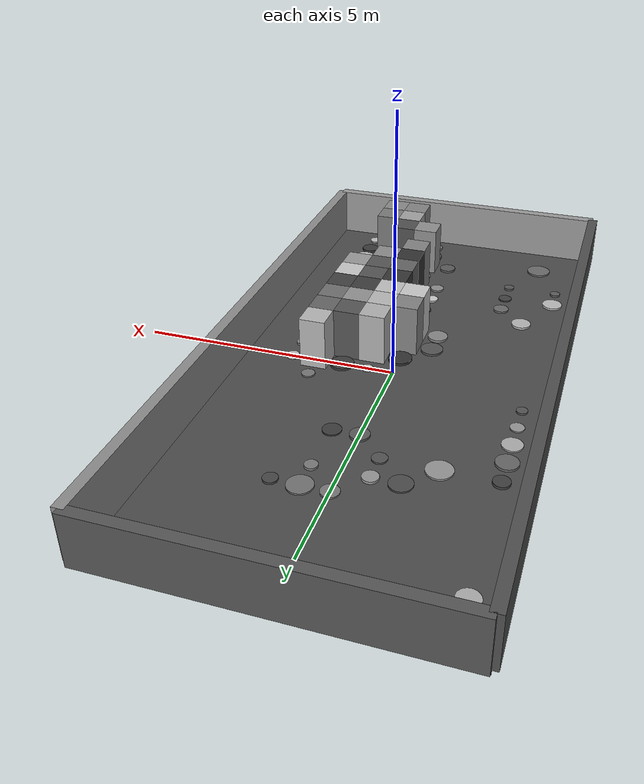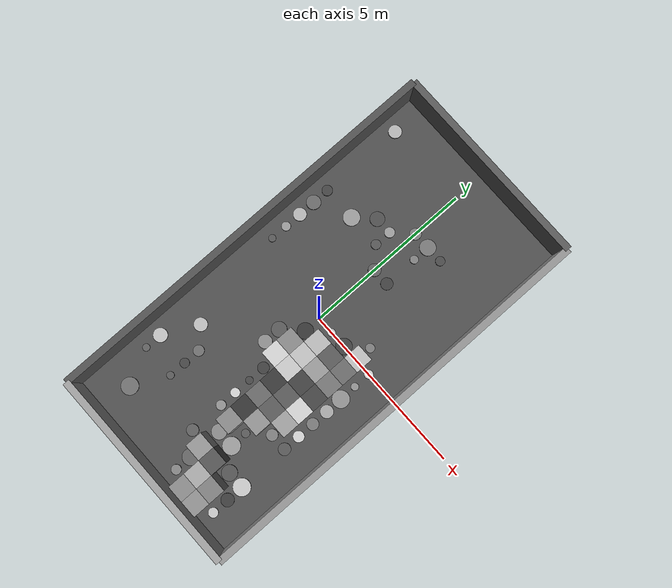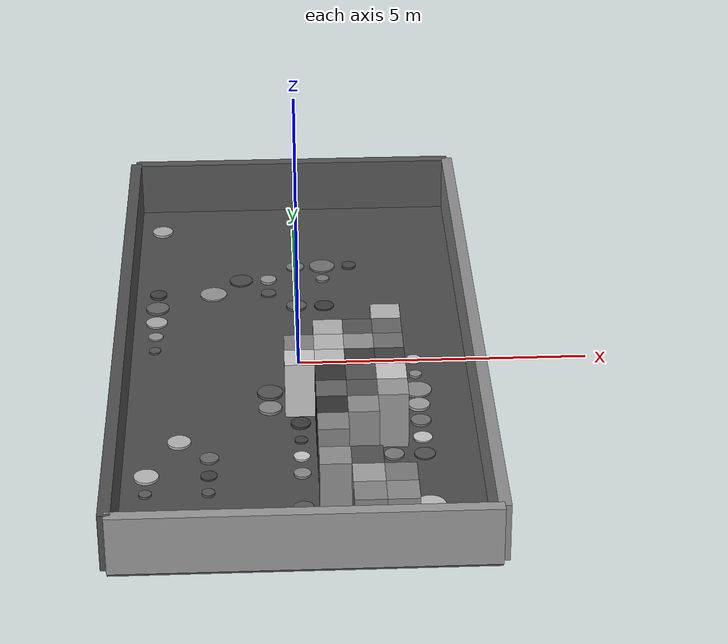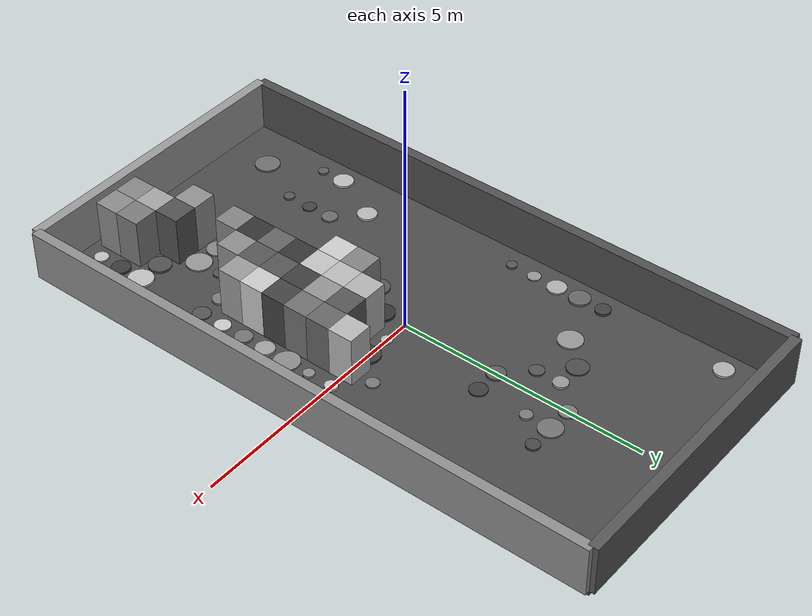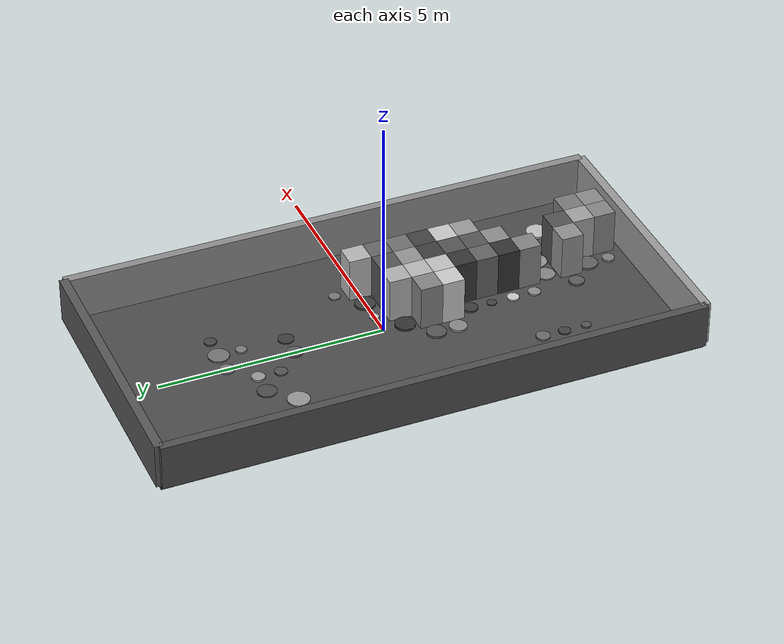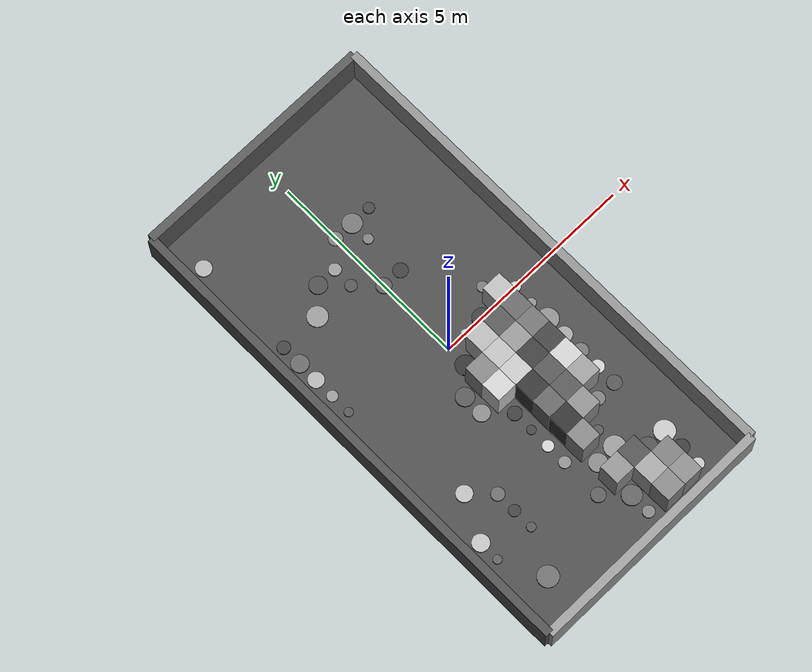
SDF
<sdf version="1.7">
  <world name="default">
    <plugin filename="gz-sim-physics-system" name="gz::sim::systems::Physics" />
    <plugin filename="gz-sim-user-commands-system" name="gz::sim::systems::UserCommands" />
    <plugin filename="gz-sim-scene-broadcaster-system" name="gz::sim::systems::SceneBroadcaster" />
    <plugin filename="gz-sim-sensors-system" name="gz::sim::systems::Sensors">
      <render_engine>ogre2</render_engine>
    </plugin>
    <plugin filename="gz-sim-imu-system" name="gz::sim::systems::Imu" />
    <plugin filename="gz-sim-contact-system" name="gz::sim::systems::Contact" />
    <light name="sun" type="directional">
      <cast_shadows>true</cast_shadows>
      <direction>-0.5 -0.5 -1</direction>
      <diffuse>1 1 1 1</diffuse>
      <specular>0.1 0.1 0.1 1</specular>
      <intensity>1.0</intensity>
    </light>
    <physics type="ode">
      <max_step_size>0.001</max_step_size>
      <real_time_factor>1.0</real_time_factor>
      <ode>
        <solver>
          <type>quick</type>
          <iters>150</iters>
          <precon_iters>0</precon_iters>
          <sor>1.4</sor>
          <use_dynamic_moi_rescaling>1</use_dynamic_moi_rescaling>
        </solver>
        <constraints>
          <cfm>0.00001</cfm>
          <erp>0.2</erp>
          <contact_max_correcting_vel>2000.0</contact_max_correcting_vel>
          <contact_surface_layer>0.01</contact_surface_layer>
        </constraints>
      </ode>
    </physics>
    <model name="ground_plane">
      <static>true</static>
      <link name="link">
        <pose>0.0 0.0 -0.05 0 0 0</pose>
        <visual name="visual">
          <material>
            <ambient>0.297790706906946 0.297790706906946 0.297790706906946 1</ambient>
            <diffuse>0.297790706906946 0.297790706906946 0.297790706906946 1</diffuse>
          </material>
          <geometry>
            <box>
              <size>6.0 12.0 0.1</size>
            </box>
          </geometry>
        </visual>
        <collision name="collision">
          <geometry>
            <box>
              <size>6.0 12.0 0.1</size>
            </box>
          </geometry>
          <surface>
            <friction>
              <ode>
                <mu>100</mu>
                <mu2>50.0</mu2>
                <slip1>0.0</slip1>
                <slip2>0.0</slip2>
              </ode>
            </friction>
            <bounce />
            <contact>
              <ode>
                <kp>10000.0</kp>
                <kd>100.0</kd>
              </ode>
            </contact>
          </surface>
        </collision>
      </link>
    </model>
    <model name="pn_pillar_0">
      <static>true</static>
      <link name="link">
        <pose>-2.5 -4.0 0.020492834980723545 0 0 0</pose>
        <visual name="visual">
          <material>
            <ambient>0.3650175910214716 0.3650175910214716 0.3650175910214716 1</ambient>
            <diffuse>0.3650175910214716 0.3650175910214716 0.3650175910214716 1</diffuse>
          </material>
          <geometry>
            <cylinder>
              <radius>0.10375161328340005</radius>
              <length>0.04098566996144709</length>
            </cylinder>
          </geometry>
        </visual>
        <collision name="collision">
          <geometry>
            <cylinder>
              <radius>0.10375161328340005</radius>
              <length>0.04098566996144709</length>
            </cylinder>
          </geometry>
          <surface>
            <friction>
              <ode>
                <mu>100</mu>
                <mu2>50.0</mu2>
                <slip1>0.0</slip1>
                <slip2>0.0</slip2>
              </ode>
            </friction>
            <bounce />
            <contact>
              <ode>
                <kp>10000.0</kp>
                <kd>100.0</kd>
              </ode>
            </contact>
          </surface>
        </collision>
      </link>
    </model>
    <model name="pn_pillar_1">
      <static>true</static>
      <link name="link">
        <pose>-2.5 -3.5 0.021705890177050158 0 0 0</pose>
        <visual name="visual">
          <material>
            <ambient>0.7353077406229074 0.7353077406229074 0.7353077406229074 1</ambient>
            <diffuse>0.7353077406229074 0.7353077406229074 0.7353077406229074 1</diffuse>
          </material>
          <geometry>
            <cylinder>
              <radius>0.2015049231134367</radius>
              <length>0.043411780354100316</length>
            </cylinder>
          </geometry>
        </visual>
        <collision name="collision">
          <geometry>
            <cylinder>
              <radius>0.2015049231134367</radius>
              <length>0.043411780354100316</length>
            </cylinder>
          </geometry>
          <surface>
            <friction>
              <ode>
                <mu>100</mu>
                <mu2>50.0</mu2>
                <slip1>0.0</slip1>
                <slip2>0.0</slip2>
              </ode>
            </friction>
            <bounce />
            <contact>
              <ode>
                <kp>10000.0</kp>
                <kd>100.0</kd>
              </ode>
            </contact>
          </surface>
        </collision>
      </link>
    </model>
    <model name="pn_pillar_2">
      <static>true</static>
      <link name="link">
        <pose>-2.5 0.5 0.017774022746065883 0 0 0</pose>
        <visual name="visual">
          <material>
            <ambient>0.331182784882162 0.331182784882162 0.331182784882162 1</ambient>
            <diffuse>0.331182784882162 0.331182784882162 0.331182784882162 1</diffuse>
          </material>
          <geometry>
            <cylinder>
              <radius>0.10446958291571055</radius>
              <length>0.035548045492131766</length>
            </cylinder>
          </geometry>
        </visual>
        <collision name="collision">
          <geometry>
            <cylinder>
              <radius>0.10446958291571055</radius>
              <length>0.035548045492131766</length>
            </cylinder>
          </geometry>
          <surface>
            <friction>
              <ode>
                <mu>100</mu>
                <mu2>50.0</mu2>
                <slip1>0.0</slip1>
                <slip2>0.0</slip2>
              </ode>
            </friction>
            <bounce />
            <contact>
              <ode>
                <kp>10000.0</kp>
                <kd>100.0</kd>
              </ode>
            </contact>
          </surface>
        </collision>
      </link>
    </model>
    <model name="pn_pillar_3">
      <static>true</static>
      <link name="link">
        <pose>-2.5 1.0 0.012831699621048296 0 0 0</pose>
        <visual name="visual">
          <material>
            <ambient>0.589930662667714 0.589930662667714 0.589930662667714 1</ambient>
            <diffuse>0.589930662667714 0.589930662667714 0.589930662667714 1</diffuse>
          </material>
          <geometry>
            <cylinder>
              <radius>0.12982564760299728</radius>
              <length>0.025663399242096593</length>
            </cylinder>
          </geometry>
        </visual>
        <collision name="collision">
          <geometry>
            <cylinder>
              <radius>0.12982564760299728</radius>
              <length>0.025663399242096593</length>
            </cylinder>
          </geometry>
          <surface>
            <friction>
              <ode>
                <mu>100</mu>
                <mu2>50.0</mu2>
                <slip1>0.0</slip1>
                <slip2>0.0</slip2>
              </ode>
            </friction>
            <bounce />
            <contact>
              <ode>
                <kp>10000.0</kp>
                <kd>100.0</kd>
              </ode>
            </contact>
          </surface>
        </collision>
      </link>
    </model>
    <model name="pn_pillar_4">
      <static>true</static>
      <link name="link">
        <pose>-2.5 1.5 0.015255507775508709 0 0 0</pose>
        <visual name="visual">
          <material>
            <ambient>0.6856582740066961 0.6856582740066961 0.6856582740066961 1</ambient>
            <diffuse>0.6856582740066961 0.6856582740066961 0.6856582740066961 1</diffuse>
          </material>
          <geometry>
            <cylinder>
              <radius>0.1883898525813863</radius>
              <length>0.030511015551017418</length>
            </cylinder>
          </geometry>
        </visual>
        <collision name="collision">
          <geometry>
            <cylinder>
              <radius>0.1883898525813863</radius>
              <length>0.030511015551017418</length>
            </cylinder>
          </geometry>
          <surface>
            <friction>
              <ode>
                <mu>100</mu>
                <mu2>50.0</mu2>
                <slip1>0.0</slip1>
                <slip2>0.0</slip2>
              </ode>
            </friction>
            <bounce />
            <contact>
              <ode>
                <kp>10000.0</kp>
                <kd>100.0</kd>
              </ode>
            </contact>
          </surface>
        </collision>
      </link>
    </model>
    <model name="pn_pillar_5">
      <static>true</static>
      <link name="link">
        <pose>-2.5 2.0 0.0225727406479101 0 0 0</pose>
        <visual name="visual">
          <material>
            <ambient>0.40415030991079515 0.40415030991079515 0.40415030991079515 1</ambient>
            <diffuse>0.40415030991079515 0.40415030991079515 0.40415030991079515 1</diffuse>
          </material>
          <geometry>
            <cylinder>
              <radius>0.20472090924823405</radius>
              <length>0.0451454812958202</length>
            </cylinder>
          </geometry>
        </visual>
        <collision name="collision">
          <geometry>
            <cylinder>
              <radius>0.20472090924823405</radius>
              <length>0.0451454812958202</length>
            </cylinder>
          </geometry>
          <surface>
            <friction>
              <ode>
                <mu>100</mu>
                <mu2>50.0</mu2>
                <slip1>0.0</slip1>
                <slip2>0.0</slip2>
              </ode>
            </friction>
            <bounce />
            <contact>
              <ode>
                <kp>10000.0</kp>
                <kd>100.0</kd>
              </ode>
            </contact>
          </surface>
        </collision>
      </link>
    </model>
    <model name="pn_pillar_6">
      <static>true</static>
      <link name="link">
        <pose>-2.5 2.5 0.024465163402584766 0 0 0</pose>
        <visual name="visual">
          <material>
            <ambient>0.2556475060280888 0.2556475060280888 0.2556475060280888 1</ambient>
            <diffuse>0.2556475060280888 0.2556475060280888 0.2556475060280888 1</diffuse>
          </material>
          <geometry>
            <cylinder>
              <radius>0.15048918176689402</radius>
              <length>0.04893032680516953</length>
            </cylinder>
          </geometry>
        </visual>
        <collision name="collision">
          <geometry>
            <cylinder>
              <radius>0.15048918176689402</radius>
              <length>0.04893032680516953</length>
            </cylinder>
          </geometry>
          <surface>
            <friction>
              <ode>
                <mu>100</mu>
                <mu2>50.0</mu2>
                <slip1>0.0</slip1>
                <slip2>0.0</slip2>
              </ode>
            </friction>
            <bounce />
            <contact>
              <ode>
                <kp>10000.0</kp>
                <kd>100.0</kd>
              </ode>
            </contact>
          </surface>
        </collision>
      </link>
    </model>
    <model name="pn_pillar_7">
      <static>true</static>
      <link name="link">
        <pose>-2.5 5.0 0.02309367957934325 0 0 0</pose>
        <visual name="visual">
          <material>
            <ambient>0.6842769639646282 0.6842769639646282 0.6842769639646282 1</ambient>
            <diffuse>0.6842769639646282 0.6842769639646282 0.6842769639646282 1</diffuse>
          </material>
          <geometry>
            <cylinder>
              <radius>0.19055890470503367</radius>
              <length>0.0461873591586865</length>
            </cylinder>
          </geometry>
        </visual>
        <collision name="collision">
          <geometry>
            <cylinder>
              <radius>0.19055890470503367</radius>
              <length>0.0461873591586865</length>
            </cylinder>
          </geometry>
          <surface>
            <friction>
              <ode>
                <mu>100</mu>
                <mu2>50.0</mu2>
                <slip1>0.0</slip1>
                <slip2>0.0</slip2>
              </ode>
            </friction>
            <bounce />
            <contact>
              <ode>
                <kp>10000.0</kp>
                <kd>100.0</kd>
              </ode>
            </contact>
          </surface>
        </collision>
      </link>
    </model>
    <model name="pn_pillar_8">
      <static>true</static>
      <link name="link">
        <pose>-2.0 -5.0 0.01920285114318376 0 0 0</pose>
        <visual name="visual">
          <material>
            <ambient>0.42712062632501213 0.42712062632501213 0.42712062632501213 1</ambient>
            <diffuse>0.42712062632501213 0.42712062632501213 0.42712062632501213 1</diffuse>
          </material>
          <geometry>
            <cylinder>
              <radius>0.2459673645969056</radius>
              <length>0.03840570228636752</length>
            </cylinder>
          </geometry>
        </visual>
        <collision name="collision">
          <geometry>
            <cylinder>
              <radius>0.2459673645969056</radius>
              <length>0.03840570228636752</length>
            </cylinder>
          </geometry>
          <surface>
            <friction>
              <ode>
                <mu>100</mu>
                <mu2>50.0</mu2>
                <slip1>0.0</slip1>
                <slip2>0.0</slip2>
              </ode>
            </friction>
            <bounce />
            <contact>
              <ode>
                <kp>10000.0</kp>
                <kd>100.0</kd>
              </ode>
            </contact>
          </surface>
        </collision>
      </link>
    </model>
    <model name="pn_pillar_9">
      <static>true</static>
      <link name="link">
        <pose>-2.0 -2.5 0.022867558303162436 0 0 0</pose>
        <visual name="visual">
          <material>
            <ambient>0.7170241401864663 0.7170241401864663 0.7170241401864663 1</ambient>
            <diffuse>0.7170241401864663 0.7170241401864663 0.7170241401864663 1</diffuse>
          </material>
          <geometry>
            <cylinder>
              <radius>0.19277796285463691</radius>
              <length>0.04573511660632487</length>
            </cylinder>
          </geometry>
        </visual>
        <collision name="collision">
          <geometry>
            <cylinder>
              <radius>0.19277796285463691</radius>
              <length>0.04573511660632487</length>
            </cylinder>
          </geometry>
          <surface>
            <friction>
              <ode>
                <mu>100</mu>
                <mu2>50.0</mu2>
                <slip1>0.0</slip1>
                <slip2>0.0</slip2>
              </ode>
            </friction>
            <bounce />
            <contact>
              <ode>
                <kp>10000.0</kp>
                <kd>100.0</kd>
              </ode>
            </contact>
          </surface>
        </collision>
      </link>
    </model>
    <model name="pn_pillar_10">
      <static>true</static>
      <link name="link">
        <pose>-1.5 -4.0 0.021307147952686546 0 0 0</pose>
        <visual name="visual">
          <material>
            <ambient>0.3367389653909282 0.3367389653909282 0.3367389653909282 1</ambient>
            <diffuse>0.3367389653909282 0.3367389653909282 0.3367389653909282 1</diffuse>
          </material>
          <geometry>
            <cylinder>
              <radius>0.10687365754834934</radius>
              <length>0.04261429590537309</length>
            </cylinder>
          </geometry>
        </visual>
        <collision name="collision">
          <geometry>
            <cylinder>
              <radius>0.10687365754834934</radius>
              <length>0.04261429590537309</length>
            </cylinder>
          </geometry>
          <surface>
            <friction>
              <ode>
                <mu>100</mu>
                <mu2>50.0</mu2>
                <slip1>0.0</slip1>
                <slip2>0.0</slip2>
              </ode>
            </friction>
            <bounce />
            <contact>
              <ode>
                <kp>10000.0</kp>
                <kd>100.0</kd>
              </ode>
            </contact>
          </surface>
        </collision>
      </link>
    </model>
    <model name="pn_pillar_11">
      <static>true</static>
      <link name="link">
        <pose>-1.5 -3.5 0.013497399711545344 0 0 0</pose>
        <visual name="visual">
          <material>
            <ambient>0.2606008576458375 0.2606008576458375 0.2606008576458375 1</ambient>
            <diffuse>0.2606008576458375 0.2606008576458375 0.2606008576458375 1</diffuse>
          </material>
          <geometry>
            <cylinder>
              <radius>0.13491863295415452</radius>
              <length>0.026994799423090687</length>
            </cylinder>
          </geometry>
        </visual>
        <collision name="collision">
          <geometry>
            <cylinder>
              <radius>0.13491863295415452</radius>
              <length>0.026994799423090687</length>
            </cylinder>
          </geometry>
          <surface>
            <friction>
              <ode>
                <mu>100</mu>
                <mu2>50.0</mu2>
                <slip1>0.0</slip1>
                <slip2>0.0</slip2>
              </ode>
            </friction>
            <bounce />
            <contact>
              <ode>
                <kp>10000.0</kp>
                <kd>100.0</kd>
              </ode>
            </contact>
          </surface>
        </collision>
      </link>
    </model>
    <model name="pn_pillar_12">
      <static>true</static>
      <link name="link">
        <pose>-1.5 -3.0 0.020446055553305004 0 0 0</pose>
        <visual name="visual">
          <material>
            <ambient>0.42210858027012965 0.42210858027012965 0.42210858027012965 1</ambient>
            <diffuse>0.42210858027012965 0.42210858027012965 0.42210858027012965 1</diffuse>
          </material>
          <geometry>
            <cylinder>
              <radius>0.15472482684551264</radius>
              <length>0.04089211110661001</length>
            </cylinder>
          </geometry>
        </visual>
        <collision name="collision">
          <geometry>
            <cylinder>
              <radius>0.15472482684551264</radius>
              <length>0.04089211110661001</length>
            </cylinder>
          </geometry>
          <surface>
            <friction>
              <ode>
                <mu>100</mu>
                <mu2>50.0</mu2>
                <slip1>0.0</slip1>
                <slip2>0.0</slip2>
              </ode>
            </friction>
            <bounce />
            <contact>
              <ode>
                <kp>10000.0</kp>
                <kd>100.0</kd>
              </ode>
            </contact>
          </surface>
        </collision>
      </link>
    </model>
    <model name="pn_pillar_13">
      <static>true</static>
      <link name="link">
        <pose>-1.5 2.5 0.01583722277561392 0 0 0</pose>
        <visual name="visual">
          <material>
            <ambient>0.5888212311479561 0.5888212311479561 0.5888212311479561 1</ambient>
            <diffuse>0.5888212311479561 0.5888212311479561 0.5888212311479561 1</diffuse>
          </material>
          <geometry>
            <cylinder>
              <radius>0.2404981881568741</radius>
              <length>0.03167444555122784</length>
            </cylinder>
          </geometry>
        </visual>
        <collision name="collision">
          <geometry>
            <cylinder>
              <radius>0.2404981881568741</radius>
              <length>0.03167444555122784</length>
            </cylinder>
          </geometry>
          <surface>
            <friction>
              <ode>
                <mu>100</mu>
                <mu2>50.0</mu2>
                <slip1>0.0</slip1>
                <slip2>0.0</slip2>
              </ode>
            </friction>
            <bounce />
            <contact>
              <ode>
                <kp>10000.0</kp>
                <kd>100.0</kd>
              </ode>
            </contact>
          </surface>
        </collision>
      </link>
    </model>
    <model name="pn_pillar_14">
      <static>true</static>
      <link name="link">
        <pose>-1.0 3.0 0.014639233102476213 0 0 0</pose>
        <visual name="visual">
          <material>
            <ambient>0.29804149625715703 0.29804149625715703 0.29804149625715703 1</ambient>
            <diffuse>0.29804149625715703 0.29804149625715703 0.29804149625715703 1</diffuse>
          </material>
          <geometry>
            <cylinder>
              <radius>0.2093690196925524</radius>
              <length>0.029278466204952426</length>
            </cylinder>
          </geometry>
        </visual>
        <collision name="collision">
          <geometry>
            <cylinder>
              <radius>0.2093690196925524</radius>
              <length>0.029278466204952426</length>
            </cylinder>
          </geometry>
          <surface>
            <friction>
              <ode>
                <mu>100</mu>
                <mu2>50.0</mu2>
                <slip1>0.0</slip1>
                <slip2>0.0</slip2>
              </ode>
            </friction>
            <bounce />
            <contact>
              <ode>
                <kp>10000.0</kp>
                <kd>100.0</kd>
              </ode>
            </contact>
          </surface>
        </collision>
      </link>
    </model>
    <model name="pn_pillar_15">
      <static>true</static>
      <link name="link">
        <pose>-0.5 -1.5 0.02486904188295744 0 0 0</pose>
        <visual name="visual">
          <material>
            <ambient>0.5341698462647878 0.5341698462647878 0.5341698462647878 1</ambient>
            <diffuse>0.5341698462647878 0.5341698462647878 0.5341698462647878 1</diffuse>
          </material>
          <geometry>
            <cylinder>
              <radius>0.19599996397811392</radius>
              <length>0.04973808376591488</length>
            </cylinder>
          </geometry>
        </visual>
        <collision name="collision">
          <geometry>
            <cylinder>
              <radius>0.19599996397811392</radius>
              <length>0.04973808376591488</length>
            </cylinder>
          </geometry>
          <surface>
            <friction>
              <ode>
                <mu>100</mu>
                <mu2>50.0</mu2>
                <slip1>0.0</slip1>
                <slip2>0.0</slip2>
              </ode>
            </friction>
            <bounce />
            <contact>
              <ode>
                <kp>10000.0</kp>
                <kd>100.0</kd>
              </ode>
            </contact>
          </surface>
        </collision>
      </link>
    </model>
    <model name="pn_pillar_16">
      <static>true</static>
      <link name="link">
        <pose>-0.5 -1.0 0.02303564900237262 0 0 0</pose>
        <visual name="visual">
          <material>
            <ambient>0.33742884317846267 0.33742884317846267 0.33742884317846267 1</ambient>
            <diffuse>0.33742884317846267 0.33742884317846267 0.33742884317846267 1</diffuse>
          </material>
          <geometry>
            <cylinder>
              <radius>0.21639998673193672</radius>
              <length>0.04607129800474524</length>
            </cylinder>
          </geometry>
        </visual>
        <collision name="collision">
          <geometry>
            <cylinder>
              <radius>0.21639998673193672</radius>
              <length>0.04607129800474524</length>
            </cylinder>
          </geometry>
          <surface>
            <friction>
              <ode>
                <mu>100</mu>
                <mu2>50.0</mu2>
                <slip1>0.0</slip1>
                <slip2>0.0</slip2>
              </ode>
            </friction>
            <bounce />
            <contact>
              <ode>
                <kp>10000.0</kp>
                <kd>100.0</kd>
              </ode>
            </contact>
          </surface>
        </collision>
      </link>
    </model>
    <model name="pn_pillar_17">
      <static>true</static>
      <link name="link">
        <pose>-0.5 2.5 0.016443163100738525 0 0 0</pose>
        <visual name="visual">
          <material>
            <ambient>0.32658970615179594 0.32658970615179594 0.32658970615179594 1</ambient>
            <diffuse>0.32658970615179594 0.32658970615179594 0.32658970615179594 1</diffuse>
          </material>
          <geometry>
            <cylinder>
              <radius>0.14016113139635542</radius>
              <length>0.03288632620147705</length>
            </cylinder>
          </geometry>
        </visual>
        <collision name="collision">
          <geometry>
            <cylinder>
              <radius>0.14016113139635542</radius>
              <length>0.03288632620147705</length>
            </cylinder>
          </geometry>
          <surface>
            <friction>
              <ode>
                <mu>100</mu>
                <mu2>50.0</mu2>
                <slip1>0.0</slip1>
                <slip2>0.0</slip2>
              </ode>
            </friction>
            <bounce />
            <contact>
              <ode>
                <kp>10000.0</kp>
                <kd>100.0</kd>
              </ode>
            </contact>
          </surface>
        </collision>
      </link>
    </model>
    <model name="pn_pillar_18">
      <static>true</static>
      <link name="link">
        <pose>-0.5 3.0 0.02345459533090836 0 0 0</pose>
        <visual name="visual">
          <material>
            <ambient>0.5932631991769282 0.5932631991769282 0.5932631991769282 1</ambient>
            <diffuse>0.5932631991769282 0.5932631991769282 0.5932631991769282 1</diffuse>
          </material>
          <geometry>
            <cylinder>
              <radius>0.1472016821197717</radius>
              <length>0.04690919066181672</length>
            </cylinder>
          </geometry>
        </visual>
        <collision name="collision">
          <geometry>
            <cylinder>
              <radius>0.1472016821197717</radius>
              <length>0.04690919066181672</length>
            </cylinder>
          </geometry>
          <surface>
            <friction>
              <ode>
                <mu>100</mu>
                <mu2>50.0</mu2>
                <slip1>0.0</slip1>
                <slip2>0.0</slip2>
              </ode>
            </friction>
            <bounce />
            <contact>
              <ode>
                <kp>10000.0</kp>
                <kd>100.0</kd>
              </ode>
            </contact>
          </surface>
        </collision>
      </link>
    </model>
    <model name="pn_pillar_19">
      <static>true</static>
      <link name="link">
        <pose>0.0 -4.5 0.023931844871756796 0 0 0</pose>
        <visual name="visual">
          <material>
            <ambient>0.3589280998988315 0.3589280998988315 0.3589280998988315 1</ambient>
            <diffuse>0.3589280998988315 0.3589280998988315 0.3589280998988315 1</diffuse>
          </material>
          <geometry>
            <cylinder>
              <radius>0.16882777788810982</radius>
              <length>0.04786368974351359</length>
            </cylinder>
          </geometry>
        </visual>
        <collision name="collision">
          <geometry>
            <cylinder>
              <radius>0.16882777788810982</radius>
              <length>0.04786368974351359</length>
            </cylinder>
          </geometry>
          <surface>
            <friction>
              <ode>
                <mu>100</mu>
                <mu2>50.0</mu2>
                <slip1>0.0</slip1>
                <slip2>0.0</slip2>
              </ode>
            </friction>
            <bounce />
            <contact>
              <ode>
                <kp>10000.0</kp>
                <kd>100.0</kd>
              </ode>
            </contact>
          </surface>
        </collision>
      </link>
    </model>
    <model name="pn_pillar_20">
      <static>true</static>
      <link name="link">
        <pose>0.0 -3.5 0.019517101677039385 0 0 0</pose>
        <visual name="visual">
          <material>
            <ambient>0.5507515941341243 0.5507515941341243 0.5507515941341243 1</ambient>
            <diffuse>0.5507515941341243 0.5507515941341243 0.5507515941341243 1</diffuse>
          </material>
          <geometry>
            <cylinder>
              <radius>0.1394112412784403</radius>
              <length>0.03903420335407877</length>
            </cylinder>
          </geometry>
        </visual>
        <collision name="collision">
          <geometry>
            <cylinder>
              <radius>0.1394112412784403</radius>
              <length>0.03903420335407877</length>
            </cylinder>
          </geometry>
          <surface>
            <friction>
              <ode>
                <mu>100</mu>
                <mu2>50.0</mu2>
                <slip1>0.0</slip1>
                <slip2>0.0</slip2>
              </ode>
            </friction>
            <bounce />
            <contact>
              <ode>
                <kp>10000.0</kp>
                <kd>100.0</kd>
              </ode>
            </contact>
          </surface>
        </collision>
      </link>
    </model>
    <model name="pn_pillar_21">
      <static>true</static>
      <link name="link">
        <pose>0.0 -3.0 0.017492506314254967 0 0 0</pose>
        <visual name="visual">
          <material>
            <ambient>0.7985225638970663 0.7985225638970663 0.7985225638970663 1</ambient>
            <diffuse>0.7985225638970663 0.7985225638970663 0.7985225638970663 1</diffuse>
          </material>
          <geometry>
            <cylinder>
              <radius>0.13289811387359252</radius>
              <length>0.034985012628509934</length>
            </cylinder>
          </geometry>
        </visual>
        <collision name="collision">
          <geometry>
            <cylinder>
              <radius>0.13289811387359252</radius>
              <length>0.034985012628509934</length>
            </cylinder>
          </geometry>
          <surface>
            <friction>
              <ode>
                <mu>100</mu>
                <mu2>50.0</mu2>
                <slip1>0.0</slip1>
                <slip2>0.0</slip2>
              </ode>
            </friction>
            <bounce />
            <contact>
              <ode>
                <kp>10000.0</kp>
                <kd>100.0</kd>
              </ode>
            </contact>
          </surface>
        </collision>
      </link>
    </model>
    <model name="pn_pillar_22">
      <static>true</static>
      <link name="link">
        <pose>0.0 -2.5 0.013636367652172424 0 0 0</pose>
        <visual name="visual">
          <material>
            <ambient>0.2657894782103955 0.2657894782103955 0.2657894782103955 1</ambient>
            <diffuse>0.2657894782103955 0.2657894782103955 0.2657894782103955 1</diffuse>
          </material>
          <geometry>
            <cylinder>
              <radius>0.10706745631371019</radius>
              <length>0.027272735304344847</length>
            </cylinder>
          </geometry>
        </visual>
        <collision name="collision">
          <geometry>
            <cylinder>
              <radius>0.10706745631371019</radius>
              <length>0.027272735304344847</length>
            </cylinder>
          </geometry>
          <surface>
            <friction>
              <ode>
                <mu>100</mu>
                <mu2>50.0</mu2>
                <slip1>0.0</slip1>
                <slip2>0.0</slip2>
              </ode>
            </friction>
            <bounce />
            <contact>
              <ode>
                <kp>10000.0</kp>
                <kd>100.0</kd>
              </ode>
            </contact>
          </surface>
        </collision>
      </link>
    </model>
    <model name="pn_pillar_23">
      <static>true</static>
      <link name="link">
        <pose>0.0 -2.0 0.022400992054537053 0 0 0</pose>
        <visual name="visual">
          <material>
            <ambient>0.2381166236911743 0.2381166236911743 0.2381166236911743 1</ambient>
            <diffuse>0.2381166236911743 0.2381166236911743 0.2381166236911743 1</diffuse>
          </material>
          <geometry>
            <cylinder>
              <radius>0.1633239950199526</radius>
              <length>0.04480198410907411</length>
            </cylinder>
          </geometry>
        </visual>
        <collision name="collision">
          <geometry>
            <cylinder>
              <radius>0.1633239950199526</radius>
              <length>0.04480198410907411</length>
            </cylinder>
          </geometry>
          <surface>
            <friction>
              <ode>
                <mu>100</mu>
                <mu2>50.0</mu2>
                <slip1>0.0</slip1>
                <slip2>0.0</slip2>
              </ode>
            </friction>
            <bounce />
            <contact>
              <ode>
                <kp>10000.0</kp>
                <kd>100.0</kd>
              </ode>
            </contact>
          </surface>
        </collision>
      </link>
    </model>
    <model name="pn_wall_24">
      <static>true</static>
      <link name="link">
        <pose>0.0 -1.5 0.5 0 0 0</pose>
        <visual name="visual">
          <material>
            <ambient>0.7976728281440582 0.7976728281440582 0.7976728281440582 1</ambient>
            <diffuse>0.7976728281440582 0.7976728281440582 0.7976728281440582 1</diffuse>
          </material>
          <geometry>
            <box>
              <size>0.5 0.5 1.0</size>
            </box>
          </geometry>
        </visual>
        <collision name="collision">
          <geometry>
            <box>
              <size>0.5 0.5 1.0</size>
            </box>
          </geometry>
          <surface>
            <friction>
              <ode>
                <mu>100</mu>
                <mu2>50.0</mu2>
                <slip1>0.0</slip1>
                <slip2>0.0</slip2>
              </ode>
            </friction>
            <bounce />
            <contact>
              <ode>
                <kp>10000.0</kp>
                <kd>100.0</kd>
              </ode>
            </contact>
          </surface>
        </collision>
      </link>
    </model>
    <model name="pn_wall_25">
      <static>true</static>
      <link name="link">
        <pose>0.0 -1.0 0.5 0 0 0</pose>
        <visual name="visual">
          <material>
            <ambient>0.5174686070594823 0.5174686070594823 0.5174686070594823 1</ambient>
            <diffuse>0.5174686070594823 0.5174686070594823 0.5174686070594823 1</diffuse>
          </material>
          <geometry>
            <box>
              <size>0.5 0.5 1.0</size>
            </box>
          </geometry>
        </visual>
        <collision name="collision">
          <geometry>
            <box>
              <size>0.5 0.5 1.0</size>
            </box>
          </geometry>
          <surface>
            <friction>
              <ode>
                <mu>100</mu>
                <mu2>50.0</mu2>
                <slip1>0.0</slip1>
                <slip2>0.0</slip2>
              </ode>
            </friction>
            <bounce />
            <contact>
              <ode>
                <kp>10000.0</kp>
                <kd>100.0</kd>
              </ode>
            </contact>
          </surface>
        </collision>
      </link>
    </model>
    <model name="pn_pillar_26">
      <static>true</static>
      <link name="link">
        <pose>0.0 -0.5 0.024638479720170227 0 0 0</pose>
        <visual name="visual">
          <material>
            <ambient>0.2068886131656918 0.2068886131656918 0.2068886131656918 1</ambient>
            <diffuse>0.2068886131656918 0.2068886131656918 0.2068886131656918 1</diffuse>
          </material>
          <geometry>
            <cylinder>
              <radius>0.2291169553351747</radius>
              <length>0.049276959440340454</length>
            </cylinder>
          </geometry>
        </visual>
        <collision name="collision">
          <geometry>
            <cylinder>
              <radius>0.2291169553351747</radius>
              <length>0.049276959440340454</length>
            </cylinder>
          </geometry>
          <surface>
            <friction>
              <ode>
                <mu>100</mu>
                <mu2>50.0</mu2>
                <slip1>0.0</slip1>
                <slip2>0.0</slip2>
              </ode>
            </friction>
            <bounce />
            <contact>
              <ode>
                <kp>10000.0</kp>
                <kd>100.0</kd>
              </ode>
            </contact>
          </surface>
        </collision>
      </link>
    </model>
    <model name="pn_pillar_27">
      <static>true</static>
      <link name="link">
        <pose>0.0 2.0 0.021021379612832188 0 0 0</pose>
        <visual name="visual">
          <material>
            <ambient>0.3600951139715257 0.3600951139715257 0.3600951139715257 1</ambient>
            <diffuse>0.3600951139715257 0.3600951139715257 0.3600951139715257 1</diffuse>
          </material>
          <geometry>
            <cylinder>
              <radius>0.1805455495613193</radius>
              <length>0.042042759225664375</length>
            </cylinder>
          </geometry>
        </visual>
        <collision name="collision">
          <geometry>
            <cylinder>
              <radius>0.1805455495613193</radius>
              <length>0.042042759225664375</length>
            </cylinder>
          </geometry>
          <surface>
            <friction>
              <ode>
                <mu>100</mu>
                <mu2>50.0</mu2>
                <slip1>0.0</slip1>
                <slip2>0.0</slip2>
              </ode>
            </friction>
            <bounce />
            <contact>
              <ode>
                <kp>10000.0</kp>
                <kd>100.0</kd>
              </ode>
            </contact>
          </surface>
        </collision>
      </link>
    </model>
    <model name="pn_pillar_28">
      <static>true</static>
      <link name="link">
        <pose>0.0 3.5 0.013894402169948456 0 0 0</pose>
        <visual name="visual">
          <material>
            <ambient>0.47223422379752394 0.47223422379752394 0.47223422379752394 1</ambient>
            <diffuse>0.47223422379752394 0.47223422379752394 0.47223422379752394 1</diffuse>
          </material>
          <geometry>
            <cylinder>
              <radius>0.16521478760036573</radius>
              <length>0.027788804339896913</length>
            </cylinder>
          </geometry>
        </visual>
        <collision name="collision">
          <geometry>
            <cylinder>
              <radius>0.16521478760036573</radius>
              <length>0.027788804339896913</length>
            </cylinder>
          </geometry>
          <surface>
            <friction>
              <ode>
                <mu>100</mu>
                <mu2>50.0</mu2>
                <slip1>0.0</slip1>
                <slip2>0.0</slip2>
              </ode>
            </friction>
            <bounce />
            <contact>
              <ode>
                <kp>10000.0</kp>
                <kd>100.0</kd>
              </ode>
            </contact>
          </surface>
        </collision>
      </link>
    </model>
    <model name="pn_pillar_29">
      <static>true</static>
      <link name="link">
        <pose>0.5 -5.5 0.02344816175472743 0 0 0</pose>
        <visual name="visual">
          <material>
            <ambient>0.500351667830179 0.500351667830179 0.500351667830179 1</ambient>
            <diffuse>0.500351667830179 0.500351667830179 0.500351667830179 1</diffuse>
          </material>
          <geometry>
            <cylinder>
              <radius>0.1395083576126636</radius>
              <length>0.04689632350945486</length>
            </cylinder>
          </geometry>
        </visual>
        <collision name="collision">
          <geometry>
            <cylinder>
              <radius>0.1395083576126636</radius>
              <length>0.04689632350945486</length>
            </cylinder>
          </geometry>
          <surface>
            <friction>
              <ode>
                <mu>100</mu>
                <mu2>50.0</mu2>
                <slip1>0.0</slip1>
                <slip2>0.0</slip2>
              </ode>
            </friction>
            <bounce />
            <contact>
              <ode>
                <kp>10000.0</kp>
                <kd>100.0</kd>
              </ode>
            </contact>
          </surface>
        </collision>
      </link>
    </model>
    <model name="pn_pillar_30">
      <static>true</static>
      <link name="link">
        <pose>0.5 -5.0 0.02390784799181026 0 0 0</pose>
        <visual name="visual">
          <material>
            <ambient>0.3790668748691798 0.3790668748691798 0.3790668748691798 1</ambient>
            <diffuse>0.3790668748691798 0.3790668748691798 0.3790668748691798 1</diffuse>
          </material>
          <geometry>
            <cylinder>
              <radius>0.23057778547551502</radius>
              <length>0.04781569598362052</length>
            </cylinder>
          </geometry>
        </visual>
        <collision name="collision">
          <geometry>
            <cylinder>
              <radius>0.23057778547551502</radius>
              <length>0.04781569598362052</length>
            </cylinder>
          </geometry>
          <surface>
            <friction>
              <ode>
                <mu>100</mu>
                <mu2>50.0</mu2>
                <slip1>0.0</slip1>
                <slip2>0.0</slip2>
              </ode>
            </friction>
            <bounce />
            <contact>
              <ode>
                <kp>10000.0</kp>
                <kd>100.0</kd>
              </ode>
            </contact>
          </surface>
        </collision>
      </link>
    </model>
    <model name="pn_wall_31">
      <static>true</static>
      <link name="link">
        <pose>0.5 -4.5 0.5 0 0 0</pose>
        <visual name="visual">
          <material>
            <ambient>0.5653821268629035 0.5653821268629035 0.5653821268629035 1</ambient>
            <diffuse>0.5653821268629035 0.5653821268629035 0.5653821268629035 1</diffuse>
          </material>
          <geometry>
            <box>
              <size>0.5 0.5 1.0</size>
            </box>
          </geometry>
        </visual>
        <collision name="collision">
          <geometry>
            <box>
              <size>0.5 0.5 1.0</size>
            </box>
          </geometry>
          <surface>
            <friction>
              <ode>
                <mu>100</mu>
                <mu2>50.0</mu2>
                <slip1>0.0</slip1>
                <slip2>0.0</slip2>
              </ode>
            </friction>
            <bounce />
            <contact>
              <ode>
                <kp>10000.0</kp>
                <kd>100.0</kd>
              </ode>
            </contact>
          </surface>
        </collision>
      </link>
    </model>
    <model name="pn_pillar_32">
      <static>true</static>
      <link name="link">
        <pose>0.5 -4.0 0.014410490856870435 0 0 0</pose>
        <visual name="visual">
          <material>
            <ambient>0.5236274180717755 0.5236274180717755 0.5236274180717755 1</ambient>
            <diffuse>0.5236274180717755 0.5236274180717755 0.5236274180717755 1</diffuse>
          </material>
          <geometry>
            <cylinder>
              <radius>0.2143766200112727</radius>
              <length>0.02882098171374087</length>
            </cylinder>
          </geometry>
        </visual>
        <collision name="collision">
          <geometry>
            <cylinder>
              <radius>0.2143766200112727</radius>
              <length>0.02882098171374087</length>
            </cylinder>
          </geometry>
          <surface>
            <friction>
              <ode>
                <mu>100</mu>
                <mu2>50.0</mu2>
                <slip1>0.0</slip1>
                <slip2>0.0</slip2>
              </ode>
            </friction>
            <bounce />
            <contact>
              <ode>
                <kp>10000.0</kp>
                <kd>100.0</kd>
              </ode>
            </contact>
          </surface>
        </collision>
      </link>
    </model>
    <model name="pn_wall_33">
      <static>true</static>
      <link name="link">
        <pose>0.5 -3.5 0.5 0 0 0</pose>
        <visual name="visual">
          <material>
            <ambient>0.5182122033171066 0.5182122033171066 0.5182122033171066 1</ambient>
            <diffuse>0.5182122033171066 0.5182122033171066 0.5182122033171066 1</diffuse>
          </material>
          <geometry>
            <box>
              <size>0.5 0.5 1.0</size>
            </box>
          </geometry>
        </visual>
        <collision name="collision">
          <geometry>
            <box>
              <size>0.5 0.5 1.0</size>
            </box>
          </geometry>
          <surface>
            <friction>
              <ode>
                <mu>100</mu>
                <mu2>50.0</mu2>
                <slip1>0.0</slip1>
                <slip2>0.0</slip2>
              </ode>
            </friction>
            <bounce />
            <contact>
              <ode>
                <kp>10000.0</kp>
                <kd>100.0</kd>
              </ode>
            </contact>
          </surface>
        </collision>
      </link>
    </model>
    <model name="pn_wall_34">
      <static>true</static>
      <link name="link">
        <pose>0.5 -3.0 0.5 0 0 0</pose>
        <visual name="visual">
          <material>
            <ambient>0.20034313767676612 0.20034313767676612 0.20034313767676612 1</ambient>
            <diffuse>0.20034313767676612 0.20034313767676612 0.20034313767676612 1</diffuse>
          </material>
          <geometry>
            <box>
              <size>0.5 0.5 1.0</size>
            </box>
          </geometry>
        </visual>
        <collision name="collision">
          <geometry>
            <box>
              <size>0.5 0.5 1.0</size>
            </box>
          </geometry>
          <surface>
            <friction>
              <ode>
                <mu>100</mu>
                <mu2>50.0</mu2>
                <slip1>0.0</slip1>
                <slip2>0.0</slip2>
              </ode>
            </friction>
            <bounce />
            <contact>
              <ode>
                <kp>10000.0</kp>
                <kd>100.0</kd>
              </ode>
            </contact>
          </surface>
        </collision>
      </link>
    </model>
    <model name="pn_wall_35">
      <static>true</static>
      <link name="link">
        <pose>0.5 -2.5 0.5 0 0 0</pose>
        <visual name="visual">
          <material>
            <ambient>0.3944936342028039 0.3944936342028039 0.3944936342028039 1</ambient>
            <diffuse>0.3944936342028039 0.3944936342028039 0.3944936342028039 1</diffuse>
          </material>
          <geometry>
            <box>
              <size>0.5 0.5 1.0</size>
            </box>
          </geometry>
        </visual>
        <collision name="collision">
          <geometry>
            <box>
              <size>0.5 0.5 1.0</size>
            </box>
          </geometry>
          <surface>
            <friction>
              <ode>
                <mu>100</mu>
                <mu2>50.0</mu2>
                <slip1>0.0</slip1>
                <slip2>0.0</slip2>
              </ode>
            </friction>
            <bounce />
            <contact>
              <ode>
                <kp>10000.0</kp>
                <kd>100.0</kd>
              </ode>
            </contact>
          </surface>
        </collision>
      </link>
    </model>
    <model name="pn_wall_36">
      <static>true</static>
      <link name="link">
        <pose>0.5 -2.0 0.5 0 0 0</pose>
        <visual name="visual">
          <material>
            <ambient>0.21168604543149938 0.21168604543149938 0.21168604543149938 1</ambient>
            <diffuse>0.21168604543149938 0.21168604543149938 0.21168604543149938 1</diffuse>
          </material>
          <geometry>
            <box>
              <size>0.5 0.5 1.0</size>
            </box>
          </geometry>
        </visual>
        <collision name="collision">
          <geometry>
            <box>
              <size>0.5 0.5 1.0</size>
            </box>
          </geometry>
          <surface>
            <friction>
              <ode>
                <mu>100</mu>
                <mu2>50.0</mu2>
                <slip1>0.0</slip1>
                <slip2>0.0</slip2>
              </ode>
            </friction>
            <bounce />
            <contact>
              <ode>
                <kp>10000.0</kp>
                <kd>100.0</kd>
              </ode>
            </contact>
          </surface>
        </collision>
      </link>
    </model>
    <model name="pn_wall_37">
      <static>true</static>
      <link name="link">
        <pose>0.5 -1.5 0.5 0 0 0</pose>
        <visual name="visual">
          <material>
            <ambient>0.7574591697587703 0.7574591697587703 0.7574591697587703 1</ambient>
            <diffuse>0.7574591697587703 0.7574591697587703 0.7574591697587703 1</diffuse>
          </material>
          <geometry>
            <box>
              <size>0.5 0.5 1.0</size>
            </box>
          </geometry>
        </visual>
        <collision name="collision">
          <geometry>
            <box>
              <size>0.5 0.5 1.0</size>
            </box>
          </geometry>
          <surface>
            <friction>
              <ode>
                <mu>100</mu>
                <mu2>50.0</mu2>
                <slip1>0.0</slip1>
                <slip2>0.0</slip2>
              </ode>
            </friction>
            <bounce />
            <contact>
              <ode>
                <kp>10000.0</kp>
                <kd>100.0</kd>
              </ode>
            </contact>
          </surface>
        </collision>
      </link>
    </model>
    <model name="pn_wall_38">
      <static>true</static>
      <link name="link">
        <pose>0.5 -1.0 0.5 0 0 0</pose>
        <visual name="visual">
          <material>
            <ambient>0.7272331266939107 0.7272331266939107 0.7272331266939107 1</ambient>
            <diffuse>0.7272331266939107 0.7272331266939107 0.7272331266939107 1</diffuse>
          </material>
          <geometry>
            <box>
              <size>0.5 0.5 1.0</size>
            </box>
          </geometry>
        </visual>
        <collision name="collision">
          <geometry>
            <box>
              <size>0.5 0.5 1.0</size>
            </box>
          </geometry>
          <surface>
            <friction>
              <ode>
                <mu>100</mu>
                <mu2>50.0</mu2>
                <slip1>0.0</slip1>
                <slip2>0.0</slip2>
              </ode>
            </friction>
            <bounce />
            <contact>
              <ode>
                <kp>10000.0</kp>
                <kd>100.0</kd>
              </ode>
            </contact>
          </surface>
        </collision>
      </link>
    </model>
    <model name="pn_wall_39">
      <static>true</static>
      <link name="link">
        <pose>0.5 -0.5 0.5 0 0 0</pose>
        <visual name="visual">
          <material>
            <ambient>0.6989993176167077 0.6989993176167077 0.6989993176167077 1</ambient>
            <diffuse>0.6989993176167077 0.6989993176167077 0.6989993176167077 1</diffuse>
          </material>
          <geometry>
            <box>
              <size>0.5 0.5 1.0</size>
            </box>
          </geometry>
        </visual>
        <collision name="collision">
          <geometry>
            <box>
              <size>0.5 0.5 1.0</size>
            </box>
          </geometry>
          <surface>
            <friction>
              <ode>
                <mu>100</mu>
                <mu2>50.0</mu2>
                <slip1>0.0</slip1>
                <slip2>0.0</slip2>
              </ode>
            </friction>
            <bounce />
            <contact>
              <ode>
                <kp>10000.0</kp>
                <kd>100.0</kd>
              </ode>
            </contact>
          </surface>
        </collision>
      </link>
    </model>
    <model name="pn_pillar_40">
      <static>true</static>
      <link name="link">
        <pose>0.5 0.0 0.01634392656753327 0 0 0</pose>
        <visual name="visual">
          <material>
            <ambient>0.7268057595224244 0.7268057595224244 0.7268057595224244 1</ambient>
            <diffuse>0.7268057595224244 0.7268057595224244 0.7268057595224244 1</diffuse>
          </material>
          <geometry>
            <cylinder>
              <radius>0.10868877497412814</radius>
              <length>0.03268785313506654</length>
            </cylinder>
          </geometry>
        </visual>
        <collision name="collision">
          <geometry>
            <cylinder>
              <radius>0.10868877497412814</radius>
              <length>0.03268785313506654</length>
            </cylinder>
          </geometry>
          <surface>
            <friction>
              <ode>
                <mu>100</mu>
                <mu2>50.0</mu2>
                <slip1>0.0</slip1>
                <slip2>0.0</slip2>
              </ode>
            </friction>
            <bounce />
            <contact>
              <ode>
                <kp>10000.0</kp>
                <kd>100.0</kd>
              </ode>
            </contact>
          </surface>
        </collision>
      </link>
    </model>
    <model name="pn_pillar_41">
      <static>true</static>
      <link name="link">
        <pose>0.5 2.0 0.013570668150848486 0 0 0</pose>
        <visual name="visual">
          <material>
            <ambient>0.24152751108103018 0.24152751108103018 0.24152751108103018 1</ambient>
            <diffuse>0.24152751108103018 0.24152751108103018 0.24152751108103018 1</diffuse>
          </material>
          <geometry>
            <cylinder>
              <radius>0.17289856949749205</radius>
              <length>0.02714133630169697</length>
            </cylinder>
          </geometry>
        </visual>
        <collision name="collision">
          <geometry>
            <cylinder>
              <radius>0.17289856949749205</radius>
              <length>0.02714133630169697</length>
            </cylinder>
          </geometry>
          <surface>
            <friction>
              <ode>
                <mu>100</mu>
                <mu2>50.0</mu2>
                <slip1>0.0</slip1>
                <slip2>0.0</slip2>
              </ode>
            </friction>
            <bounce />
            <contact>
              <ode>
                <kp>10000.0</kp>
                <kd>100.0</kd>
              </ode>
            </contact>
          </surface>
        </collision>
      </link>
    </model>
    <model name="pn_pillar_42">
      <static>true</static>
      <link name="link">
        <pose>0.5 3.0 0.022072930366337347 0 0 0</pose>
        <visual name="visual">
          <material>
            <ambient>0.48516942685923886 0.48516942685923886 0.48516942685923886 1</ambient>
            <diffuse>0.48516942685923886 0.48516942685923886 0.48516942685923886 1</diffuse>
          </material>
          <geometry>
            <cylinder>
              <radius>0.11925871967496443</radius>
              <length>0.044145860732674694</length>
            </cylinder>
          </geometry>
        </visual>
        <collision name="collision">
          <geometry>
            <cylinder>
              <radius>0.11925871967496443</radius>
              <length>0.044145860732674694</length>
            </cylinder>
          </geometry>
          <surface>
            <friction>
              <ode>
                <mu>100</mu>
                <mu2>50.0</mu2>
                <slip1>0.0</slip1>
                <slip2>0.0</slip2>
              </ode>
            </friction>
            <bounce />
            <contact>
              <ode>
                <kp>10000.0</kp>
                <kd>100.0</kd>
              </ode>
            </contact>
          </surface>
        </collision>
      </link>
    </model>
    <model name="pn_pillar_43">
      <static>true</static>
      <link name="link">
        <pose>0.5 3.5 0.01581320786175074 0 0 0</pose>
        <visual name="visual">
          <material>
            <ambient>0.4538827641205322 0.4538827641205322 0.4538827641205322 1</ambient>
            <diffuse>0.4538827641205322 0.4538827641205322 0.4538827641205322 1</diffuse>
          </material>
          <geometry>
            <cylinder>
              <radius>0.23086495616278863</radius>
              <length>0.03162641572350148</length>
            </cylinder>
          </geometry>
        </visual>
        <collision name="collision">
          <geometry>
            <cylinder>
              <radius>0.23086495616278863</radius>
              <length>0.03162641572350148</length>
            </cylinder>
          </geometry>
          <surface>
            <friction>
              <ode>
                <mu>100</mu>
                <mu2>50.0</mu2>
                <slip1>0.0</slip1>
                <slip2>0.0</slip2>
              </ode>
            </friction>
            <bounce />
            <contact>
              <ode>
                <kp>10000.0</kp>
                <kd>100.0</kd>
              </ode>
            </contact>
          </surface>
        </collision>
      </link>
    </model>
    <model name="pn_wall_44">
      <static>true</static>
      <link name="link">
        <pose>1.0 -5.5 0.5 0 0 0</pose>
        <visual name="visual">
          <material>
            <ambient>0.523577653267675 0.523577653267675 0.523577653267675 1</ambient>
            <diffuse>0.523577653267675 0.523577653267675 0.523577653267675 1</diffuse>
          </material>
          <geometry>
            <box>
              <size>0.5 0.5 1.0</size>
            </box>
          </geometry>
        </visual>
        <collision name="collision">
          <geometry>
            <box>
              <size>0.5 0.5 1.0</size>
            </box>
          </geometry>
          <surface>
            <friction>
              <ode>
                <mu>100</mu>
                <mu2>50.0</mu2>
                <slip1>0.0</slip1>
                <slip2>0.0</slip2>
              </ode>
            </friction>
            <bounce />
            <contact>
              <ode>
                <kp>10000.0</kp>
                <kd>100.0</kd>
              </ode>
            </contact>
          </surface>
        </collision>
      </link>
    </model>
    <model name="pn_wall_45">
      <static>true</static>
      <link name="link">
        <pose>1.0 -5.0 0.5 0 0 0</pose>
        <visual name="visual">
          <material>
            <ambient>0.6379586414539857 0.6379586414539857 0.6379586414539857 1</ambient>
            <diffuse>0.6379586414539857 0.6379586414539857 0.6379586414539857 1</diffuse>
          </material>
          <geometry>
            <box>
              <size>0.5 0.5 1.0</size>
            </box>
          </geometry>
        </visual>
        <collision name="collision">
          <geometry>
            <box>
              <size>0.5 0.5 1.0</size>
            </box>
          </geometry>
          <surface>
            <friction>
              <ode>
                <mu>100</mu>
                <mu2>50.0</mu2>
                <slip1>0.0</slip1>
                <slip2>0.0</slip2>
              </ode>
            </friction>
            <bounce />
            <contact>
              <ode>
                <kp>10000.0</kp>
                <kd>100.0</kd>
              </ode>
            </contact>
          </surface>
        </collision>
      </link>
    </model>
    <model name="pn_wall_46">
      <static>true</static>
      <link name="link">
        <pose>1.0 -4.5 0.5 0 0 0</pose>
        <visual name="visual">
          <material>
            <ambient>0.3206906380338176 0.3206906380338176 0.3206906380338176 1</ambient>
            <diffuse>0.3206906380338176 0.3206906380338176 0.3206906380338176 1</diffuse>
          </material>
          <geometry>
            <box>
              <size>0.5 0.5 1.0</size>
            </box>
          </geometry>
        </visual>
        <collision name="collision">
          <geometry>
            <box>
              <size>0.5 0.5 1.0</size>
            </box>
          </geometry>
          <surface>
            <friction>
              <ode>
                <mu>100</mu>
                <mu2>50.0</mu2>
                <slip1>0.0</slip1>
                <slip2>0.0</slip2>
              </ode>
            </friction>
            <bounce />
            <contact>
              <ode>
                <kp>10000.0</kp>
                <kd>100.0</kd>
              </ode>
            </contact>
          </surface>
        </collision>
      </link>
    </model>
    <model name="pn_pillar_47">
      <static>true</static>
      <link name="link">
        <pose>1.0 -4.0 0.01639645364126119 0 0 0</pose>
        <visual name="visual">
          <material>
            <ambient>0.5899268345836721 0.5899268345836721 0.5899268345836721 1</ambient>
            <diffuse>0.5899268345836721 0.5899268345836721 0.5899268345836721 1</diffuse>
          </material>
          <geometry>
            <cylinder>
              <radius>0.2492724034991342</radius>
              <length>0.03279290728252238</length>
            </cylinder>
          </geometry>
        </visual>
        <collision name="collision">
          <geometry>
            <cylinder>
              <radius>0.2492724034991342</radius>
              <length>0.03279290728252238</length>
            </cylinder>
          </geometry>
          <surface>
            <friction>
              <ode>
                <mu>100</mu>
                <mu2>50.0</mu2>
                <slip1>0.0</slip1>
                <slip2>0.0</slip2>
              </ode>
            </friction>
            <bounce />
            <contact>
              <ode>
                <kp>10000.0</kp>
                <kd>100.0</kd>
              </ode>
            </contact>
          </surface>
        </collision>
      </link>
    </model>
    <model name="pn_pillar_48">
      <static>true</static>
      <link name="link">
        <pose>1.0 -3.5 0.018969698012944885 0 0 0</pose>
        <visual name="visual">
          <material>
            <ambient>0.33481840221893444 0.33481840221893444 0.33481840221893444 1</ambient>
            <diffuse>0.33481840221893444 0.33481840221893444 0.33481840221893444 1</diffuse>
          </material>
          <geometry>
            <cylinder>
              <radius>0.11815062938023986</radius>
              <length>0.03793939602588977</length>
            </cylinder>
          </geometry>
        </visual>
        <collision name="collision">
          <geometry>
            <cylinder>
              <radius>0.11815062938023986</radius>
              <length>0.03793939602588977</length>
            </cylinder>
          </geometry>
          <surface>
            <friction>
              <ode>
                <mu>100</mu>
                <mu2>50.0</mu2>
                <slip1>0.0</slip1>
                <slip2>0.0</slip2>
              </ode>
            </friction>
            <bounce />
            <contact>
              <ode>
                <kp>10000.0</kp>
                <kd>100.0</kd>
              </ode>
            </contact>
          </surface>
        </collision>
      </link>
    </model>
    <model name="pn_wall_49">
      <static>true</static>
      <link name="link">
        <pose>1.0 -3.0 0.5 0 0 0</pose>
        <visual name="visual">
          <material>
            <ambient>0.5529852310743401 0.5529852310743401 0.5529852310743401 1</ambient>
            <diffuse>0.5529852310743401 0.5529852310743401 0.5529852310743401 1</diffuse>
          </material>
          <geometry>
            <box>
              <size>0.5 0.5 1.0</size>
            </box>
          </geometry>
        </visual>
        <collision name="collision">
          <geometry>
            <box>
              <size>0.5 0.5 1.0</size>
            </box>
          </geometry>
          <surface>
            <friction>
              <ode>
                <mu>100</mu>
                <mu2>50.0</mu2>
                <slip1>0.0</slip1>
                <slip2>0.0</slip2>
              </ode>
            </friction>
            <bounce />
            <contact>
              <ode>
                <kp>10000.0</kp>
                <kd>100.0</kd>
              </ode>
            </contact>
          </surface>
        </collision>
      </link>
    </model>
    <model name="pn_wall_50">
      <static>true</static>
      <link name="link">
        <pose>1.0 -2.5 0.5 0 0 0</pose>
        <visual name="visual">
          <material>
            <ambient>0.3380688395579462 0.3380688395579462 0.3380688395579462 1</ambient>
            <diffuse>0.3380688395579462 0.3380688395579462 0.3380688395579462 1</diffuse>
          </material>
          <geometry>
            <box>
              <size>0.5 0.5 1.0</size>
            </box>
          </geometry>
        </visual>
        <collision name="collision">
          <geometry>
            <box>
              <size>0.5 0.5 1.0</size>
            </box>
          </geometry>
          <surface>
            <friction>
              <ode>
                <mu>100</mu>
                <mu2>50.0</mu2>
                <slip1>0.0</slip1>
                <slip2>0.0</slip2>
              </ode>
            </friction>
            <bounce />
            <contact>
              <ode>
                <kp>10000.0</kp>
                <kd>100.0</kd>
              </ode>
            </contact>
          </surface>
        </collision>
      </link>
    </model>
    <model name="pn_wall_51">
      <static>true</static>
      <link name="link">
        <pose>1.0 -2.0 0.5 0 0 0</pose>
        <visual name="visual">
          <material>
            <ambient>0.33213043067093573 0.33213043067093573 0.33213043067093573 1</ambient>
            <diffuse>0.33213043067093573 0.33213043067093573 0.33213043067093573 1</diffuse>
          </material>
          <geometry>
            <box>
              <size>0.5 0.5 1.0</size>
            </box>
          </geometry>
        </visual>
        <collision name="collision">
          <geometry>
            <box>
              <size>0.5 0.5 1.0</size>
            </box>
          </geometry>
          <surface>
            <friction>
              <ode>
                <mu>100</mu>
                <mu2>50.0</mu2>
                <slip1>0.0</slip1>
                <slip2>0.0</slip2>
              </ode>
            </friction>
            <bounce />
            <contact>
              <ode>
                <kp>10000.0</kp>
                <kd>100.0</kd>
              </ode>
            </contact>
          </surface>
        </collision>
      </link>
    </model>
    <model name="pn_wall_52">
      <static>true</static>
      <link name="link">
        <pose>1.0 -1.5 0.5 0 0 0</pose>
        <visual name="visual">
          <material>
            <ambient>0.24259585160541955 0.24259585160541955 0.24259585160541955 1</ambient>
            <diffuse>0.24259585160541955 0.24259585160541955 0.24259585160541955 1</diffuse>
          </material>
          <geometry>
            <box>
              <size>0.5 0.5 1.0</size>
            </box>
          </geometry>
        </visual>
        <collision name="collision">
          <geometry>
            <box>
              <size>0.5 0.5 1.0</size>
            </box>
          </geometry>
          <surface>
            <friction>
              <ode>
                <mu>100</mu>
                <mu2>50.0</mu2>
                <slip1>0.0</slip1>
                <slip2>0.0</slip2>
              </ode>
            </friction>
            <bounce />
            <contact>
              <ode>
                <kp>10000.0</kp>
                <kd>100.0</kd>
              </ode>
            </contact>
          </surface>
        </collision>
      </link>
    </model>
    <model name="pn_wall_53">
      <static>true</static>
      <link name="link">
        <pose>1.0 -1.0 0.5 0 0 0</pose>
        <visual name="visual">
          <material>
            <ambient>0.5786617743620595 0.5786617743620595 0.5786617743620595 1</ambient>
            <diffuse>0.5786617743620595 0.5786617743620595 0.5786617743620595 1</diffuse>
          </material>
          <geometry>
            <box>
              <size>0.5 0.5 1.0</size>
            </box>
          </geometry>
        </visual>
        <collision name="collision">
          <geometry>
            <box>
              <size>0.5 0.5 1.0</size>
            </box>
          </geometry>
          <surface>
            <friction>
              <ode>
                <mu>100</mu>
                <mu2>50.0</mu2>
                <slip1>0.0</slip1>
                <slip2>0.0</slip2>
              </ode>
            </friction>
            <bounce />
            <contact>
              <ode>
                <kp>10000.0</kp>
                <kd>100.0</kd>
              </ode>
            </contact>
          </surface>
        </collision>
      </link>
    </model>
    <model name="pn_wall_54">
      <static>true</static>
      <link name="link">
        <pose>1.0 -0.5 0.5 0 0 0</pose>
        <visual name="visual">
          <material>
            <ambient>0.33736507028669266 0.33736507028669266 0.33736507028669266 1</ambient>
            <diffuse>0.33736507028669266 0.33736507028669266 0.33736507028669266 1</diffuse>
          </material>
          <geometry>
            <box>
              <size>0.5 0.5 1.0</size>
            </box>
          </geometry>
        </visual>
        <collision name="collision">
          <geometry>
            <box>
              <size>0.5 0.5 1.0</size>
            </box>
          </geometry>
          <surface>
            <friction>
              <ode>
                <mu>100</mu>
                <mu2>50.0</mu2>
                <slip1>0.0</slip1>
                <slip2>0.0</slip2>
              </ode>
            </friction>
            <bounce />
            <contact>
              <ode>
                <kp>10000.0</kp>
                <kd>100.0</kd>
              </ode>
            </contact>
          </surface>
        </collision>
      </link>
    </model>
    <model name="pn_pillar_55">
      <static>true</static>
      <link name="link">
        <pose>1.0 0.0 0.0238177501625766 0 0 0</pose>
        <visual name="visual">
          <material>
            <ambient>0.2425144099331921 0.2425144099331921 0.2425144099331921 1</ambient>
            <diffuse>0.2425144099331921 0.2425144099331921 0.2425144099331921 1</diffuse>
          </material>
          <geometry>
            <cylinder>
              <radius>0.22894531003806198</radius>
              <length>0.0476355003251532</length>
            </cylinder>
          </geometry>
        </visual>
        <collision name="collision">
          <geometry>
            <cylinder>
              <radius>0.22894531003806198</radius>
              <length>0.0476355003251532</length>
            </cylinder>
          </geometry>
          <surface>
            <friction>
              <ode>
                <mu>100</mu>
                <mu2>50.0</mu2>
                <slip1>0.0</slip1>
                <slip2>0.0</slip2>
              </ode>
            </friction>
            <bounce />
            <contact>
              <ode>
                <kp>10000.0</kp>
                <kd>100.0</kd>
              </ode>
            </contact>
          </surface>
        </collision>
      </link>
    </model>
    <model name="pn_pillar_56">
      <static>true</static>
      <link name="link">
        <pose>1.0 3.5 0.020862222228703507 0 0 0</pose>
        <visual name="visual">
          <material>
            <ambient>0.27938710923501503 0.27938710923501503 0.27938710923501503 1</ambient>
            <diffuse>0.27938710923501503 0.27938710923501503 0.27938710923501503 1</diffuse>
          </material>
          <geometry>
            <cylinder>
              <radius>0.13213552110556578</radius>
              <length>0.041724444457407014</length>
            </cylinder>
          </geometry>
        </visual>
        <collision name="collision">
          <geometry>
            <cylinder>
              <radius>0.13213552110556578</radius>
              <length>0.041724444457407014</length>
            </cylinder>
          </geometry>
          <surface>
            <friction>
              <ode>
                <mu>100</mu>
                <mu2>50.0</mu2>
                <slip1>0.0</slip1>
                <slip2>0.0</slip2>
              </ode>
            </friction>
            <bounce />
            <contact>
              <ode>
                <kp>10000.0</kp>
                <kd>100.0</kd>
              </ode>
            </contact>
          </surface>
        </collision>
      </link>
    </model>
    <model name="pn_wall_57">
      <static>true</static>
      <link name="link">
        <pose>1.5 -5.5 0.5 0 0 0</pose>
        <visual name="visual">
          <material>
            <ambient>0.5426258559951708 0.5426258559951708 0.5426258559951708 1</ambient>
            <diffuse>0.5426258559951708 0.5426258559951708 0.5426258559951708 1</diffuse>
          </material>
          <geometry>
            <box>
              <size>0.5 0.5 1.0</size>
            </box>
          </geometry>
        </visual>
        <collision name="collision">
          <geometry>
            <box>
              <size>0.5 0.5 1.0</size>
            </box>
          </geometry>
          <surface>
            <friction>
              <ode>
                <mu>100</mu>
                <mu2>50.0</mu2>
                <slip1>0.0</slip1>
                <slip2>0.0</slip2>
              </ode>
            </friction>
            <bounce />
            <contact>
              <ode>
                <kp>10000.0</kp>
                <kd>100.0</kd>
              </ode>
            </contact>
          </surface>
        </collision>
      </link>
    </model>
    <model name="pn_wall_58">
      <static>true</static>
      <link name="link">
        <pose>1.5 -5.0 0.5 0 0 0</pose>
        <visual name="visual">
          <material>
            <ambient>0.48360261578707653 0.48360261578707653 0.48360261578707653 1</ambient>
            <diffuse>0.48360261578707653 0.48360261578707653 0.48360261578707653 1</diffuse>
          </material>
          <geometry>
            <box>
              <size>0.5 0.5 1.0</size>
            </box>
          </geometry>
        </visual>
        <collision name="collision">
          <geometry>
            <box>
              <size>0.5 0.5 1.0</size>
            </box>
          </geometry>
          <surface>
            <friction>
              <ode>
                <mu>100</mu>
                <mu2>50.0</mu2>
                <slip1>0.0</slip1>
                <slip2>0.0</slip2>
              </ode>
            </friction>
            <bounce />
            <contact>
              <ode>
                <kp>10000.0</kp>
                <kd>100.0</kd>
              </ode>
            </contact>
          </surface>
        </collision>
      </link>
    </model>
    <model name="pn_pillar_59">
      <static>true</static>
      <link name="link">
        <pose>1.5 -4.5 0.022307742803634418 0 0 0</pose>
        <visual name="visual">
          <material>
            <ambient>0.3142459486171266 0.3142459486171266 0.3142459486171266 1</ambient>
            <diffuse>0.3142459486171266 0.3142459486171266 0.3142459486171266 1</diffuse>
          </material>
          <geometry>
            <cylinder>
              <radius>0.2211245496649965</radius>
              <length>0.044615485607268836</length>
            </cylinder>
          </geometry>
        </visual>
        <collision name="collision">
          <geometry>
            <cylinder>
              <radius>0.2211245496649965</radius>
              <length>0.044615485607268836</length>
            </cylinder>
          </geometry>
          <surface>
            <friction>
              <ode>
                <mu>100</mu>
                <mu2>50.0</mu2>
                <slip1>0.0</slip1>
                <slip2>0.0</slip2>
              </ode>
            </friction>
            <bounce />
            <contact>
              <ode>
                <kp>10000.0</kp>
                <kd>100.0</kd>
              </ode>
            </contact>
          </surface>
        </collision>
      </link>
    </model>
    <model name="pn_pillar_60">
      <static>true</static>
      <link name="link">
        <pose>1.5 -3.0 0.01788813978007972 0 0 0</pose>
        <visual name="visual">
          <material>
            <ambient>0.480214800822005 0.480214800822005 0.480214800822005 1</ambient>
            <diffuse>0.480214800822005 0.480214800822005 0.480214800822005 1</diffuse>
          </material>
          <geometry>
            <cylinder>
              <radius>0.1635367934529881</radius>
              <length>0.03577627956015944</length>
            </cylinder>
          </geometry>
        </visual>
        <collision name="collision">
          <geometry>
            <cylinder>
              <radius>0.1635367934529881</radius>
              <length>0.03577627956015944</length>
            </cylinder>
          </geometry>
          <surface>
            <friction>
              <ode>
                <mu>100</mu>
                <mu2>50.0</mu2>
                <slip1>0.0</slip1>
                <slip2>0.0</slip2>
              </ode>
            </friction>
            <bounce />
            <contact>
              <ode>
                <kp>10000.0</kp>
                <kd>100.0</kd>
              </ode>
            </contact>
          </surface>
        </collision>
      </link>
    </model>
    <model name="pn_wall_61">
      <static>true</static>
      <link name="link">
        <pose>1.5 -2.5 0.5 0 0 0</pose>
        <visual name="visual">
          <material>
            <ambient>0.604018728375981 0.604018728375981 0.604018728375981 1</ambient>
            <diffuse>0.604018728375981 0.604018728375981 0.604018728375981 1</diffuse>
          </material>
          <geometry>
            <box>
              <size>0.5 0.5 1.0</size>
            </box>
          </geometry>
        </visual>
        <collision name="collision">
          <geometry>
            <box>
              <size>0.5 0.5 1.0</size>
            </box>
          </geometry>
          <surface>
            <friction>
              <ode>
                <mu>100</mu>
                <mu2>50.0</mu2>
                <slip1>0.0</slip1>
                <slip2>0.0</slip2>
              </ode>
            </friction>
            <bounce />
            <contact>
              <ode>
                <kp>10000.0</kp>
                <kd>100.0</kd>
              </ode>
            </contact>
          </surface>
        </collision>
      </link>
    </model>
    <model name="pn_wall_62">
      <static>true</static>
      <link name="link">
        <pose>1.5 -2.0 0.5 0 0 0</pose>
        <visual name="visual">
          <material>
            <ambient>0.7904991268195798 0.7904991268195798 0.7904991268195798 1</ambient>
            <diffuse>0.7904991268195798 0.7904991268195798 0.7904991268195798 1</diffuse>
          </material>
          <geometry>
            <box>
              <size>0.5 0.5 1.0</size>
            </box>
          </geometry>
        </visual>
        <collision name="collision">
          <geometry>
            <box>
              <size>0.5 0.5 1.0</size>
            </box>
          </geometry>
          <surface>
            <friction>
              <ode>
                <mu>100</mu>
                <mu2>50.0</mu2>
                <slip1>0.0</slip1>
                <slip2>0.0</slip2>
              </ode>
            </friction>
            <bounce />
            <contact>
              <ode>
                <kp>10000.0</kp>
                <kd>100.0</kd>
              </ode>
            </contact>
          </surface>
        </collision>
      </link>
    </model>
    <model name="pn_wall_63">
      <static>true</static>
      <link name="link">
        <pose>1.5 -1.5 0.5 0 0 0</pose>
        <visual name="visual">
          <material>
            <ambient>0.25905072269117535 0.25905072269117535 0.25905072269117535 1</ambient>
            <diffuse>0.25905072269117535 0.25905072269117535 0.25905072269117535 1</diffuse>
          </material>
          <geometry>
            <box>
              <size>0.5 0.5 1.0</size>
            </box>
          </geometry>
        </visual>
        <collision name="collision">
          <geometry>
            <box>
              <size>0.5 0.5 1.0</size>
            </box>
          </geometry>
          <surface>
            <friction>
              <ode>
                <mu>100</mu>
                <mu2>50.0</mu2>
                <slip1>0.0</slip1>
                <slip2>0.0</slip2>
              </ode>
            </friction>
            <bounce />
            <contact>
              <ode>
                <kp>10000.0</kp>
                <kd>100.0</kd>
              </ode>
            </contact>
          </surface>
        </collision>
      </link>
    </model>
    <model name="pn_wall_64">
      <static>true</static>
      <link name="link">
        <pose>1.5 -1.0 0.5 0 0 0</pose>
        <visual name="visual">
          <material>
            <ambient>0.4415727692613613 0.4415727692613613 0.4415727692613613 1</ambient>
            <diffuse>0.4415727692613613 0.4415727692613613 0.4415727692613613 1</diffuse>
          </material>
          <geometry>
            <box>
              <size>0.5 0.5 1.0</size>
            </box>
          </geometry>
        </visual>
        <collision name="collision">
          <geometry>
            <box>
              <size>0.5 0.5 1.0</size>
            </box>
          </geometry>
          <surface>
            <friction>
              <ode>
                <mu>100</mu>
                <mu2>50.0</mu2>
                <slip1>0.0</slip1>
                <slip2>0.0</slip2>
              </ode>
            </friction>
            <bounce />
            <contact>
              <ode>
                <kp>10000.0</kp>
                <kd>100.0</kd>
              </ode>
            </contact>
          </surface>
        </collision>
      </link>
    </model>
    <model name="pn_wall_65">
      <static>true</static>
      <link name="link">
        <pose>1.5 -0.5 0.5 0 0 0</pose>
        <visual name="visual">
          <material>
            <ambient>0.4035815632369779 0.4035815632369779 0.4035815632369779 1</ambient>
            <diffuse>0.4035815632369779 0.4035815632369779 0.4035815632369779 1</diffuse>
          </material>
          <geometry>
            <box>
              <size>0.5 0.5 1.0</size>
            </box>
          </geometry>
        </visual>
        <collision name="collision">
          <geometry>
            <box>
              <size>0.5 0.5 1.0</size>
            </box>
          </geometry>
          <surface>
            <friction>
              <ode>
                <mu>100</mu>
                <mu2>50.0</mu2>
                <slip1>0.0</slip1>
                <slip2>0.0</slip2>
              </ode>
            </friction>
            <bounce />
            <contact>
              <ode>
                <kp>10000.0</kp>
                <kd>100.0</kd>
              </ode>
            </contact>
          </surface>
        </collision>
      </link>
    </model>
    <model name="pn_wall_66">
      <static>true</static>
      <link name="link">
        <pose>1.5 0.0 0.5 0 0 0</pose>
        <visual name="visual">
          <material>
            <ambient>0.7170035218116748 0.7170035218116748 0.7170035218116748 1</ambient>
            <diffuse>0.7170035218116748 0.7170035218116748 0.7170035218116748 1</diffuse>
          </material>
          <geometry>
            <box>
              <size>0.5 0.5 1.0</size>
            </box>
          </geometry>
        </visual>
        <collision name="collision">
          <geometry>
            <box>
              <size>0.5 0.5 1.0</size>
            </box>
          </geometry>
          <surface>
            <friction>
              <ode>
                <mu>100</mu>
                <mu2>50.0</mu2>
                <slip1>0.0</slip1>
                <slip2>0.0</slip2>
              </ode>
            </friction>
            <bounce />
            <contact>
              <ode>
                <kp>10000.0</kp>
                <kd>100.0</kd>
              </ode>
            </contact>
          </surface>
        </collision>
      </link>
    </model>
    <model name="pn_pillar_67">
      <static>true</static>
      <link name="link">
        <pose>1.5 0.5 0.01560820417400357 0 0 0</pose>
        <visual name="visual">
          <material>
            <ambient>0.46916812869987917 0.46916812869987917 0.46916812869987917 1</ambient>
            <diffuse>0.46916812869987917 0.46916812869987917 0.46916812869987917 1</diffuse>
          </material>
          <geometry>
            <cylinder>
              <radius>0.12853133626612173</radius>
              <length>0.03121640834800714</length>
            </cylinder>
          </geometry>
        </visual>
        <collision name="collision">
          <geometry>
            <cylinder>
              <radius>0.12853133626612173</radius>
              <length>0.03121640834800714</length>
            </cylinder>
          </geometry>
          <surface>
            <friction>
              <ode>
                <mu>100</mu>
                <mu2>50.0</mu2>
                <slip1>0.0</slip1>
                <slip2>0.0</slip2>
              </ode>
            </friction>
            <bounce />
            <contact>
              <ode>
                <kp>10000.0</kp>
                <kd>100.0</kd>
              </ode>
            </contact>
          </surface>
        </collision>
      </link>
    </model>
    <model name="pn_pillar_68">
      <static>true</static>
      <link name="link">
        <pose>2.0 -5.5 0.015981814308336756 0 0 0</pose>
        <visual name="visual">
          <material>
            <ambient>0.7539593595656078 0.7539593595656078 0.7539593595656078 1</ambient>
            <diffuse>0.7539593595656078 0.7539593595656078 0.7539593595656078 1</diffuse>
          </material>
          <geometry>
            <cylinder>
              <radius>0.13747096718231508</radius>
              <length>0.03196362861667351</length>
            </cylinder>
          </geometry>
        </visual>
        <collision name="collision">
          <geometry>
            <cylinder>
              <radius>0.13747096718231508</radius>
              <length>0.03196362861667351</length>
            </cylinder>
          </geometry>
          <surface>
            <friction>
              <ode>
                <mu>100</mu>
                <mu2>50.0</mu2>
                <slip1>0.0</slip1>
                <slip2>0.0</slip2>
              </ode>
            </friction>
            <bounce />
            <contact>
              <ode>
                <kp>10000.0</kp>
                <kd>100.0</kd>
              </ode>
            </contact>
          </surface>
        </collision>
      </link>
    </model>
    <model name="pn_pillar_69">
      <static>true</static>
      <link name="link">
        <pose>2.0 -5.0 0.023266863809522885 0 0 0</pose>
        <visual name="visual">
          <material>
            <ambient>0.23035299771492876 0.23035299771492876 0.23035299771492876 1</ambient>
            <diffuse>0.23035299771492876 0.23035299771492876 0.23035299771492876 1</diffuse>
          </material>
          <geometry>
            <cylinder>
              <radius>0.18254879686747721</radius>
              <length>0.04653372761904577</length>
            </cylinder>
          </geometry>
        </visual>
        <collision name="collision">
          <geometry>
            <cylinder>
              <radius>0.18254879686747721</radius>
              <length>0.04653372761904577</length>
            </cylinder>
          </geometry>
          <surface>
            <friction>
              <ode>
                <mu>100</mu>
                <mu2>50.0</mu2>
                <slip1>0.0</slip1>
                <slip2>0.0</slip2>
              </ode>
            </friction>
            <bounce />
            <contact>
              <ode>
                <kp>10000.0</kp>
                <kd>100.0</kd>
              </ode>
            </contact>
          </surface>
        </collision>
      </link>
    </model>
    <model name="pn_pillar_70">
      <static>true</static>
      <link name="link">
        <pose>2.0 -4.5 0.0229503448134994 0 0 0</pose>
        <visual name="visual">
          <material>
            <ambient>0.7558201898048766 0.7558201898048766 0.7558201898048766 1</ambient>
            <diffuse>0.7558201898048766 0.7558201898048766 0.7558201898048766 1</diffuse>
          </material>
          <geometry>
            <cylinder>
              <radius>0.2453494385927127</radius>
              <length>0.0459006896269988</length>
            </cylinder>
          </geometry>
        </visual>
        <collision name="collision">
          <geometry>
            <cylinder>
              <radius>0.2453494385927127</radius>
              <length>0.0459006896269988</length>
            </cylinder>
          </geometry>
          <surface>
            <friction>
              <ode>
                <mu>100</mu>
                <mu2>50.0</mu2>
                <slip1>0.0</slip1>
                <slip2>0.0</slip2>
              </ode>
            </friction>
            <bounce />
            <contact>
              <ode>
                <kp>10000.0</kp>
                <kd>100.0</kd>
              </ode>
            </contact>
          </surface>
        </collision>
      </link>
    </model>
    <model name="pn_pillar_71">
      <static>true</static>
      <link name="link">
        <pose>2.0 -3.0 0.014578888882548926 0 0 0</pose>
        <visual name="visual">
          <material>
            <ambient>0.328248379519509 0.328248379519509 0.328248379519509 1</ambient>
            <diffuse>0.328248379519509 0.328248379519509 0.328248379519509 1</diffuse>
          </material>
          <geometry>
            <cylinder>
              <radius>0.17284616881760778</radius>
              <length>0.029157777765097852</length>
            </cylinder>
          </geometry>
        </visual>
        <collision name="collision">
          <geometry>
            <cylinder>
              <radius>0.17284616881760778</radius>
              <length>0.029157777765097852</length>
            </cylinder>
          </geometry>
          <surface>
            <friction>
              <ode>
                <mu>100</mu>
                <mu2>50.0</mu2>
                <slip1>0.0</slip1>
                <slip2>0.0</slip2>
              </ode>
            </friction>
            <bounce />
            <contact>
              <ode>
                <kp>10000.0</kp>
                <kd>100.0</kd>
              </ode>
            </contact>
          </surface>
        </collision>
      </link>
    </model>
    <model name="pn_pillar_72">
      <static>true</static>
      <link name="link">
        <pose>2.0 -2.5 0.013232942499652237 0 0 0</pose>
        <visual name="visual">
          <material>
            <ambient>0.7911853062678356 0.7911853062678356 0.7911853062678356 1</ambient>
            <diffuse>0.7911853062678356 0.7911853062678356 0.7911853062678356 1</diffuse>
          </material>
          <geometry>
            <cylinder>
              <radius>0.15684596784653743</radius>
              <length>0.026465884999304475</length>
            </cylinder>
          </geometry>
        </visual>
        <collision name="collision">
          <geometry>
            <cylinder>
              <radius>0.15684596784653743</radius>
              <length>0.026465884999304475</length>
            </cylinder>
          </geometry>
          <surface>
            <friction>
              <ode>
                <mu>100</mu>
                <mu2>50.0</mu2>
                <slip1>0.0</slip1>
                <slip2>0.0</slip2>
              </ode>
            </friction>
            <bounce />
            <contact>
              <ode>
                <kp>10000.0</kp>
                <kd>100.0</kd>
              </ode>
            </contact>
          </surface>
        </collision>
      </link>
    </model>
    <model name="pn_pillar_73">
      <static>true</static>
      <link name="link">
        <pose>2.0 -2.0 0.022300882524357118 0 0 0</pose>
        <visual name="visual">
          <material>
            <ambient>0.4538044915940978 0.4538044915940978 0.4538044915940978 1</ambient>
            <diffuse>0.4538044915940978 0.4538044915940978 0.4538044915940978 1</diffuse>
          </material>
          <geometry>
            <cylinder>
              <radius>0.1682512551008715</radius>
              <length>0.044601765048714236</length>
            </cylinder>
          </geometry>
        </visual>
        <collision name="collision">
          <geometry>
            <cylinder>
              <radius>0.1682512551008715</radius>
              <length>0.044601765048714236</length>
            </cylinder>
          </geometry>
          <surface>
            <friction>
              <ode>
                <mu>100</mu>
                <mu2>50.0</mu2>
                <slip1>0.0</slip1>
                <slip2>0.0</slip2>
              </ode>
            </friction>
            <bounce />
            <contact>
              <ode>
                <kp>10000.0</kp>
                <kd>100.0</kd>
              </ode>
            </contact>
          </surface>
        </collision>
      </link>
    </model>
    <model name="pn_pillar_74">
      <static>true</static>
      <link name="link">
        <pose>2.0 -1.5 0.024942783618658926 0 0 0</pose>
        <visual name="visual">
          <material>
            <ambient>0.6310449651777956 0.6310449651777956 0.6310449651777956 1</ambient>
            <diffuse>0.6310449651777956 0.6310449651777956 0.6310449651777956 1</diffuse>
          </material>
          <geometry>
            <cylinder>
              <radius>0.18336524851084274</radius>
              <length>0.04988556723731785</length>
            </cylinder>
          </geometry>
        </visual>
        <collision name="collision">
          <geometry>
            <cylinder>
              <radius>0.18336524851084274</radius>
              <length>0.04988556723731785</length>
            </cylinder>
          </geometry>
          <surface>
            <friction>
              <ode>
                <mu>100</mu>
                <mu2>50.0</mu2>
                <slip1>0.0</slip1>
                <slip2>0.0</slip2>
              </ode>
            </friction>
            <bounce />
            <contact>
              <ode>
                <kp>10000.0</kp>
                <kd>100.0</kd>
              </ode>
            </contact>
          </surface>
        </collision>
      </link>
    </model>
    <model name="pn_pillar_75">
      <static>true</static>
      <link name="link">
        <pose>2.0 -1.0 0.016208847818682055 0 0 0</pose>
        <visual name="visual">
          <material>
            <ambient>0.5475081744897539 0.5475081744897539 0.5475081744897539 1</ambient>
            <diffuse>0.5475081744897539 0.5475081744897539 0.5475081744897539 1</diffuse>
          </material>
          <geometry>
            <cylinder>
              <radius>0.24530640474537382</radius>
              <length>0.03241769563736411</length>
            </cylinder>
          </geometry>
        </visual>
        <collision name="collision">
          <geometry>
            <cylinder>
              <radius>0.24530640474537382</radius>
              <length>0.03241769563736411</length>
            </cylinder>
          </geometry>
          <surface>
            <friction>
              <ode>
                <mu>100</mu>
                <mu2>50.0</mu2>
                <slip1>0.0</slip1>
                <slip2>0.0</slip2>
              </ode>
            </friction>
            <bounce />
            <contact>
              <ode>
                <kp>10000.0</kp>
                <kd>100.0</kd>
              </ode>
            </contact>
          </surface>
        </collision>
      </link>
    </model>
    <model name="pn_pillar_76">
      <static>true</static>
      <link name="link">
        <pose>2.0 -0.5 0.021849694504738303 0 0 0</pose>
        <visual name="visual">
          <material>
            <ambient>0.5505065566753828 0.5505065566753828 0.5505065566753828 1</ambient>
            <diffuse>0.5505065566753828 0.5505065566753828 0.5505065566753828 1</diffuse>
          </material>
          <geometry>
            <cylinder>
              <radius>0.10857479093612246</radius>
              <length>0.043699389009476605</length>
            </cylinder>
          </geometry>
        </visual>
        <collision name="collision">
          <geometry>
            <cylinder>
              <radius>0.10857479093612246</radius>
              <length>0.043699389009476605</length>
            </cylinder>
          </geometry>
          <surface>
            <friction>
              <ode>
                <mu>100</mu>
                <mu2>50.0</mu2>
                <slip1>0.0</slip1>
                <slip2>0.0</slip2>
              </ode>
            </friction>
            <bounce />
            <contact>
              <ode>
                <kp>10000.0</kp>
                <kd>100.0</kd>
              </ode>
            </contact>
          </surface>
        </collision>
      </link>
    </model>
    <model name="pn_pillar_77">
      <static>true</static>
      <link name="link">
        <pose>2.0 0.0 0.023158998650603568 0 0 0</pose>
        <visual name="visual">
          <material>
            <ambient>0.7764673419646704 0.7764673419646704 0.7764673419646704 1</ambient>
            <diffuse>0.7764673419646704 0.7764673419646704 0.7764673419646704 1</diffuse>
          </material>
          <geometry>
            <cylinder>
              <radius>0.1236149091909225</radius>
              <length>0.046317997301207135</length>
            </cylinder>
          </geometry>
        </visual>
        <collision name="collision">
          <geometry>
            <cylinder>
              <radius>0.1236149091909225</radius>
              <length>0.046317997301207135</length>
            </cylinder>
          </geometry>
          <surface>
            <friction>
              <ode>
                <mu>100</mu>
                <mu2>50.0</mu2>
                <slip1>0.0</slip1>
                <slip2>0.0</slip2>
              </ode>
            </friction>
            <bounce />
            <contact>
              <ode>
                <kp>10000.0</kp>
                <kd>100.0</kd>
              </ode>
            </contact>
          </surface>
        </collision>
      </link>
    </model>
    <model name="pn_wall_78">
      <static>true</static>
      <link name="link">
        <pose>-3.0 0.0 0.5 0 0 0</pose>
        <visual name="visual">
          <material>
            <ambient>0.31149497658843395 0.31149497658843395 0.31149497658843395 1</ambient>
            <diffuse>0.31149497658843395 0.31149497658843395 0.31149497658843395 1</diffuse>
          </material>
          <geometry>
            <box>
              <size>0.2 12.0 1.0</size>
            </box>
          </geometry>
        </visual>
        <collision name="collision">
          <geometry>
            <box>
              <size>0.2 12.0 1.0</size>
            </box>
          </geometry>
          <surface>
            <friction>
              <ode>
                <mu>100</mu>
                <mu2>50.0</mu2>
                <slip1>0.0</slip1>
                <slip2>0.0</slip2>
              </ode>
            </friction>
            <bounce />
            <contact>
              <ode>
                <kp>10000.0</kp>
                <kd>100.0</kd>
              </ode>
            </contact>
          </surface>
        </collision>
      </link>
    </model>
    <model name="pn_wall_79">
      <static>true</static>
      <link name="link">
        <pose>3.0 0.0 0.5 0 0 0</pose>
        <visual name="visual">
          <material>
            <ambient>0.5570210638700166 0.5570210638700166 0.5570210638700166 1</ambient>
            <diffuse>0.5570210638700166 0.5570210638700166 0.5570210638700166 1</diffuse>
          </material>
          <geometry>
            <box>
              <size>0.2 12.0 1.0</size>
            </box>
          </geometry>
        </visual>
        <collision name="collision">
          <geometry>
            <box>
              <size>0.2 12.0 1.0</size>
            </box>
          </geometry>
          <surface>
            <friction>
              <ode>
                <mu>100</mu>
                <mu2>50.0</mu2>
                <slip1>0.0</slip1>
                <slip2>0.0</slip2>
              </ode>
            </friction>
            <bounce />
            <contact>
              <ode>
                <kp>10000.0</kp>
                <kd>100.0</kd>
              </ode>
            </contact>
          </surface>
        </collision>
      </link>
    </model>
    <model name="pn_wall_80">
      <static>true</static>
      <link name="link">
        <pose>0.0 -6.0 0.5 0 0 0</pose>
        <visual name="visual">
          <material>
            <ambient>0.6051275321624542 0.6051275321624542 0.6051275321624542 1</ambient>
            <diffuse>0.6051275321624542 0.6051275321624542 0.6051275321624542 1</diffuse>
          </material>
          <geometry>
            <box>
              <size>6.0 0.2 1.0</size>
            </box>
          </geometry>
        </visual>
        <collision name="collision">
          <geometry>
            <box>
              <size>6.0 0.2 1.0</size>
            </box>
          </geometry>
          <surface>
            <friction>
              <ode>
                <mu>100</mu>
                <mu2>50.0</mu2>
                <slip1>0.0</slip1>
                <slip2>0.0</slip2>
              </ode>
            </friction>
            <bounce />
            <contact>
              <ode>
                <kp>10000.0</kp>
                <kd>100.0</kd>
              </ode>
            </contact>
          </surface>
        </collision>
      </link>
    </model>
    <model name="pn_wall_81">
      <static>true</static>
      <link name="link">
        <pose>0.0 6.0 0.5 0 0 0</pose>
        <visual name="visual">
          <material>
            <ambient>0.3411223370005587 0.3411223370005587 0.3411223370005587 1</ambient>
            <diffuse>0.3411223370005587 0.3411223370005587 0.3411223370005587 1</diffuse>
          </material>
          <geometry>
            <box>
              <size>6.0 0.2 1.0</size>
            </box>
          </geometry>
        </visual>
        <collision name="collision">
          <geometry>
            <box>
              <size>6.0 0.2 1.0</size>
            </box>
          </geometry>
          <surface>
            <friction>
              <ode>
                <mu>100</mu>
                <mu2>50.0</mu2>
                <slip1>0.0</slip1>
                <slip2>0.0</slip2>
              </ode>
            </friction>
            <bounce />
            <contact>
              <ode>
                <kp>10000.0</kp>
                <kd>100.0</kd>
              </ode>
            </contact>
          </surface>
        </collision>
      </link>
    </model>
  </world>
</sdf>
